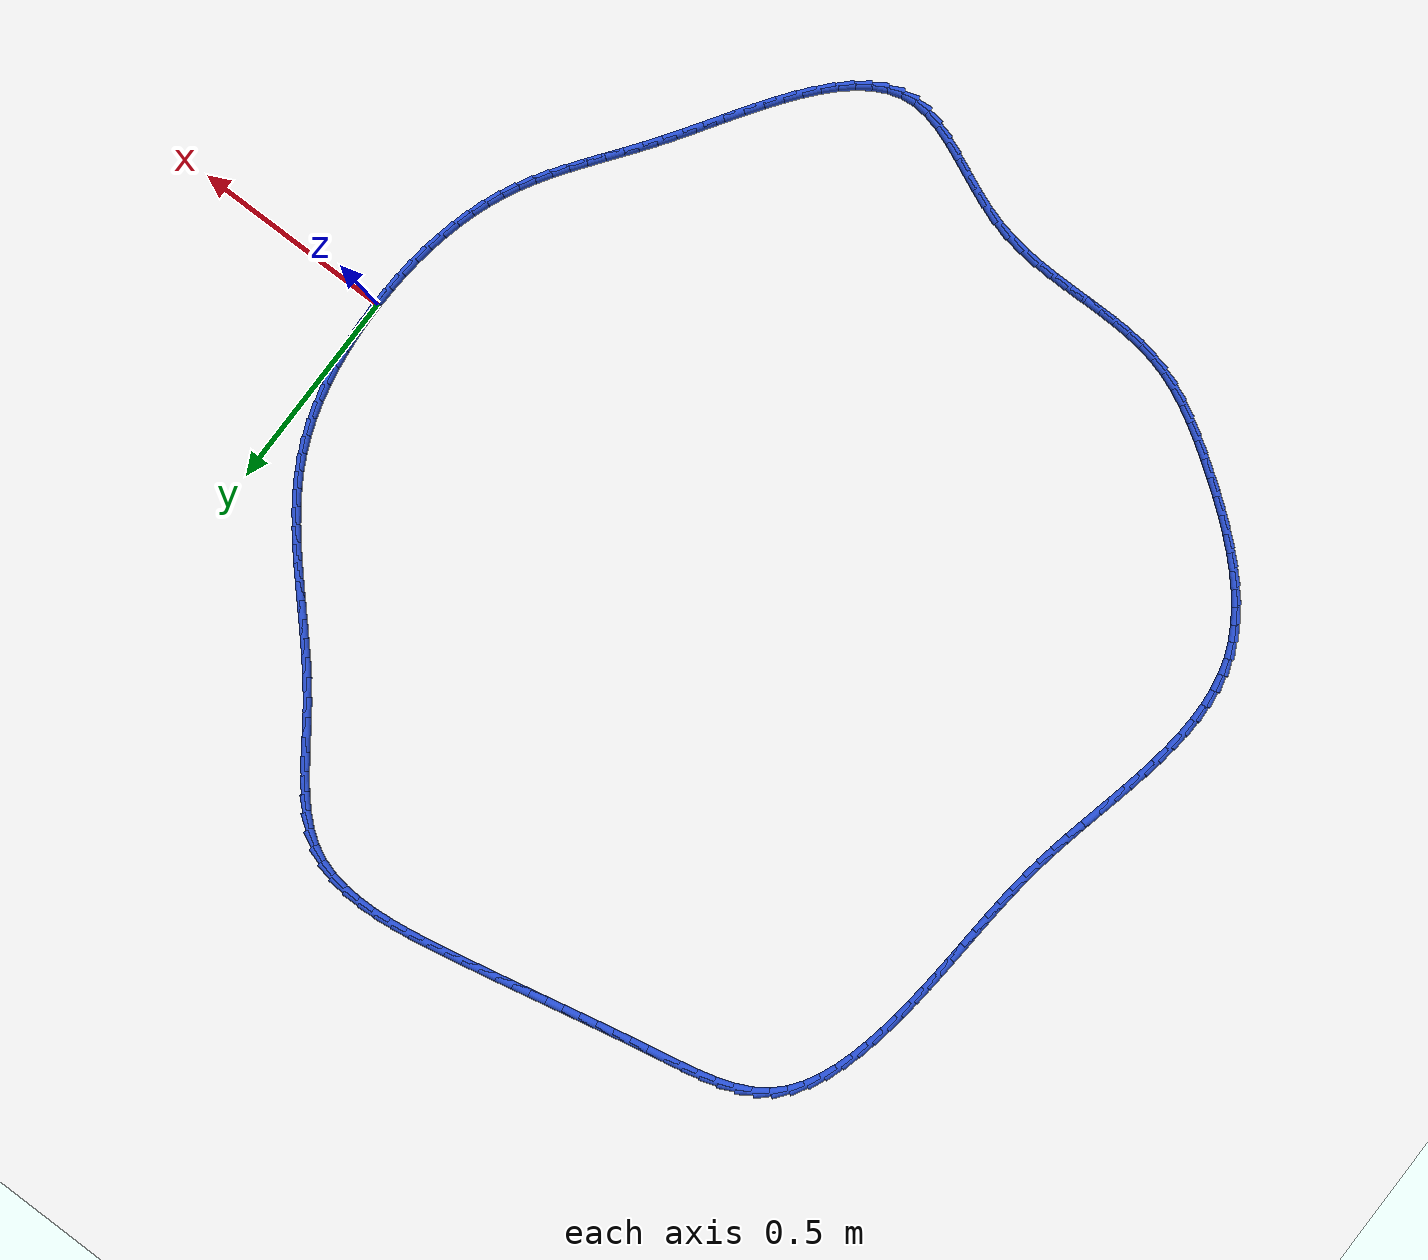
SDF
<sdf version="1.6">
 <world name="default">
  <light name="sun" type="directional">
   <pose>0 0 10 0 -0 0</pose>
   <diffuse>0.8 0.8 0.8 1</diffuse>
   <specular>0.2 0.2 0.2 1</specular>
   <attenuation>
    <range>1000</range>
    <constant>0.9</constant>
    <linear>0.01</linear>
    <quadratic>0.001</quadratic>
   </attenuation>
   <direction>-0.5 0.1 -0.9</direction>
  </light>
  <model name="ground_plane">
   <static>1</static>
   <link name="link">
    <collision name="collision">
     <geometry><plane><normal>0 0 1</normal><size>100 100</size></plane></geometry>
     <surface><friction><ode><mu>100</mu><mu2>50</mu2></ode></friction></surface>
    </collision>
    <visual name="visual">
     <cast_shadows>0</cast_shadows>
     <geometry><plane><normal>0 0 1</normal><size>100 100</size></plane></geometry>
     <material>
      <script><uri>file://media/materials/scripts/gazebo.material</uri><name>Gazebo/WhiteGlow</name></script>
     </material>
    </visual>
   </link>
  </model>
  <gravity>0 0 -9.8</gravity>
  <magnetic_field>6e-06 2.3e-05 -4.2e-05</magnetic_field>
  <atmosphere type="adiabatic"/>
  <physics name="default_physics" default="0" type="ode">
   <max_step_size>0.001</max_step_size>
   <real_time_factor>1</real_time_factor>
   <real_time_update_rate>1000</real_time_update_rate>
  </physics>
  <scene><ambient>0.4 0.4 0.4 1</ambient><background>0.7 0.7 0.7 1</background><shadows>1</shadows></scene>
  <spherical_coordinates>
   <surface_model>EARTH_WGS84</surface_model>
   <latitude_deg>0</latitude_deg>
   <longitude_deg>0</longitude_deg>
   <elevation>0</elevation>
   <heading_deg>0</heading_deg>
  </spherical_coordinates>
  <model name="line">
   <link name="link_0">
    <pose>4.336808689942018e-18 -1.3877787807814457e-17 0.01 0 1.57 -1.5573718621784105</pose>
    <collision name="collision">
     <geometry><cylinder><radius>0.01</radius><length>0.08</length></cylinder></geometry>
    </collision>
    <visual name="visual">
     <material>
      <script><name>Gazebo/Blue</name><uri>file://media/materials/scripts/gazebo.material</uri></script>
     </material>
     <geometry><cylinder><radius>0.01</radius><length>0.08</length></cylinder></geometry>
    </visual>
   </link>
   <link name="link_1">
    <pose>-0.0005983916359873998 0.04457203367264502 0.01 0 1.57 -1.5188670011490113</pose>
    <collision name="collision">
     <geometry><cylinder><radius>0.01</radius><length>0.08</length></cylinder></geometry>
    </collision>
    <visual name="visual">
     <material>
      <script><name>Gazebo/Blue</name><uri>file://media/materials/scripts/gazebo.material</uri></script>
     </material>
     <geometry><cylinder><radius>0.01</radius><length>0.08</length></cylinder></geometry>
    </visual>
   </link>
   <link name="link_2">
    <pose>-0.0029063172632489377 0.08897566622336017 0.01 0 1.57 -1.4777067448218728</pose>
    <collision name="collision">
     <geometry><cylinder><radius>0.01</radius><length>0.08</length></cylinder></geometry>
    </collision>
    <visual name="visual">
     <material>
      <script><name>Gazebo/Blue</name><uri>file://media/materials/scripts/gazebo.material</uri></script>
     </material>
     <geometry><cylinder><radius>0.01</radius><length>0.08</length></cylinder></geometry>
    </visual>
   </link>
   <link name="link_3">
    <pose>-0.007019723194135353 0.13303556172974781 0.01 0 1.57 -1.4335227655718614</pose>
    <collision name="collision">
     <geometry><cylinder><radius>0.01</radius><length>0.08</length></cylinder></geometry>
    </collision>
    <visual name="visual">
     <material>
      <script><name>Gazebo/Blue</name><uri>file://media/materials/scripts/gazebo.material</uri></script>
     </material>
     <geometry><cylinder><radius>0.01</radius><length>0.08</length></cylinder></geometry>
    </visual>
   </link>
   <link name="link_4">
    <pose>-0.013034555740997373 0.17657638426941008 0.01 0 1.57 -1.385933105360552</pose>
    <collision name="collision">
     <geometry><cylinder><radius>0.01</radius><length>0.08</length></cylinder></geometry>
    </collision>
    <visual name="visual">
     <material>
      <script><name>Gazebo/Blue</name><uri>file://media/materials/scripts/gazebo.material</uri></script>
     </material>
     <geometry><cylinder><radius>0.01</radius><length>0.08</length></cylinder></geometry>
    </visual>
   </link>
   <link name="link_5">
    <pose>-0.021046761216185737 0.21942279791994926 0.01 0 1.57 -1.3345503823095883</pose>
    <collision name="collision">
     <geometry><cylinder><radius>0.01</radius><length>0.08</length></cylinder></geometry>
    </collision>
    <visual name="visual">
     <material>
      <script><name>Gazebo/Blue</name><uri>file://media/materials/scripts/gazebo.material</uri></script>
     </material>
     <geometry><cylinder><radius>0.01</radius><length>0.08</length></cylinder></geometry>
    </visual>
   </link>
   <link name="link_6">
    <pose>-0.0311522859320512 0.26139946675896764 0.01 0 1.57 -1.2789963268459807</pose>
    <collision name="collision">
     <geometry><cylinder><radius>0.01</radius><length>0.08</length></cylinder></geometry>
    </collision>
    <visual name="visual">
     <material>
      <script><name>Gazebo/Blue</name><uri>file://media/materials/scripts/gazebo.material</uri></script>
     </material>
     <geometry><cylinder><radius>0.01</radius><length>0.08</length></cylinder></geometry>
    </visual>
   </link>
   <link name="link_7">
    <pose>-0.04344707620094446 0.3023310548640673 0.01 0 1.57 -1.2189245359871548</pose>
    <collision name="collision">
     <geometry><cylinder><radius>0.01</radius><length>0.08</length></cylinder></geometry>
    </collision>
    <visual name="visual">
     <material>
      <script><name>Gazebo/Blue</name><uri>file://media/materials/scripts/gazebo.material</uri></script>
     </material>
     <geometry><cylinder><radius>0.01</radius><length>0.08</length></cylinder></geometry>
    </visual>
   </link>
   <link name="link_8">
    <pose>-0.058027078335216295 0.34204222631285075 0.01 0 1.57 -1.1540531137541636</pose>
    <collision name="collision">
     <geometry><cylinder><radius>0.01</radius><length>0.08</length></cylinder></geometry>
    </collision>
    <visual name="visual">
     <material>
      <script><name>Gazebo/Blue</name><uri>file://media/materials/scripts/gazebo.material</uri></script>
     </material>
     <geometry><cylinder><radius>0.01</radius><length>0.08</length></cylinder></geometry>
    </visual>
   </link>
   <link name="link_9">
    <pose>-0.07498823864721739 0.38035764518291987 0.01 0 1.57 -1.0858827836086442</pose>
    <collision name="collision">
     <geometry><cylinder><radius>0.01</radius><length>0.08</length></cylinder></geometry>
    </collision>
    <visual name="visual">
     <material>
      <script><name>Gazebo/Blue</name><uri>file://media/materials/scripts/gazebo.material</uri></script>
     </material>
     <geometry><cylinder><radius>0.01</radius><length>0.08</length></cylinder></geometry>
    </visual>
   </link>
   <link name="link_10">
    <pose>-0.0943766519901181 0.4171567272831883 0.01 0 1.57 -1.0228177106142808</pose>
    <collision name="collision">
     <geometry><cylinder><radius>0.01</radius><length>0.08</length></cylinder></geometry>
    </collision>
    <visual name="visual">
     <material>
      <script><name>Gazebo/Blue</name><uri>file://media/materials/scripts/gazebo.material</uri></script>
     </material>
     <geometry><cylinder><radius>0.01</radius><length>0.08</length></cylinder></geometry>
    </visual>
   </link>
   <link name="link_11">
    <pose>-0.11599814226122311 0.4525827774046317 0.01 0 1.57 -0.9680428558615343</pose>
    <collision name="collision">
     <geometry><cylinder><radius>0.01</radius><length>0.08</length></cylinder></geometry>
    </collision>
    <visual name="visual">
     <material>
      <script><name>Gazebo/Blue</name><uri>file://media/materials/scripts/gazebo.material</uri></script>
     </material>
     <geometry><cylinder><radius>0.01</radius><length>0.08</length></cylinder></geometry>
    </visual>
   </link>
   <link name="link_12">
    <pose>-0.1395862384832859 0.4868585016157743 0.01 0 1.57 -0.921997925332311</pose>
    <collision name="collision">
     <geometry><cylinder><radius>0.01</radius><length>0.08</length></cylinder></geometry>
    </collision>
    <visual name="visual">
     <material>
      <script><name>Gazebo/Blue</name><uri>file://media/materials/scripts/gazebo.material</uri></script>
     </material>
     <geometry><cylinder><radius>0.01</radius><length>0.08</length></cylinder></geometry>
    </visual>
   </link>
   <link name="link_13">
    <pose>-0.1648744552800054 0.5202066217995853 0.01 0 1.57 -0.8848145867729409</pose>
    <collision name="collision">
     <geometry><cylinder><radius>0.01</radius><length>0.08</length></cylinder></geometry>
    </collision>
    <visual name="visual">
     <material>
      <script><name>Gazebo/Blue</name><uri>file://media/materials/scripts/gazebo.material</uri></script>
     </material>
     <geometry><cylinder><radius>0.01</radius><length>0.08</length></cylinder></geometry>
    </visual>
   </link>
   <link name="link_14">
    <pose>-0.1915963072750807 0.5528498598390348 0.01 0 1.57 -0.85642039293689</pose>
    <collision name="collision">
     <geometry><cylinder><radius>0.01</radius><length>0.08</length></cylinder></geometry>
    </collision>
    <visual name="visual">
     <material>
      <script><name>Gazebo/Blue</name><uri>file://media/materials/scripts/gazebo.material</uri></script>
     </material>
     <geometry><cylinder><radius>0.01</radius><length>0.08</length></cylinder></geometry>
    </visual>
   </link>
   <link name="link_15">
    <pose>-0.21948530909221053 0.5850109376170919 0.01 0 1.57 -0.8366287324983233</pose>
    <collision name="collision">
     <geometry><cylinder><radius>0.01</radius><length>0.08</length></cylinder></geometry>
    </collision>
    <visual name="visual">
     <material>
      <script><name>Gazebo/Blue</name><uri>file://media/materials/scripts/gazebo.material</uri></script>
     </material>
     <geometry><cylinder><radius>0.01</radius><length>0.08</length></cylinder></geometry>
    </visual>
   </link>
   <link name="link_16">
    <pose>-0.24827497535509394 0.6169125770167263 0.01 0 1.57 -0.8252062401643862</pose>
    <collision name="collision">
     <geometry><cylinder><radius>0.01</radius><length>0.08</length></cylinder></geometry>
    </collision>
    <visual name="visual">
     <material>
      <script><name>Gazebo/Blue</name><uri>file://media/materials/scripts/gazebo.material</uri></script>
     </material>
     <geometry><cylinder><radius>0.01</radius><length>0.08</length></cylinder></geometry>
    </visual>
   </link>
   <link name="link_17">
    <pose>-0.27769882068742996 0.6487774999209076 0.01 0 1.57 -0.8219165124980077</pose>
    <collision name="collision">
     <geometry><cylinder><radius>0.01</radius><length>0.08</length></cylinder></geometry>
    </collision>
    <visual name="visual">
     <material>
      <script><name>Gazebo/Blue</name><uri>file://media/materials/scripts/gazebo.material</uri></script>
     </material>
     <geometry><cylinder><radius>0.01</radius><length>0.08</length></cylinder></geometry>
    </visual>
   </link>
   <link name="link_18">
    <pose>-0.30749035971291716 0.6808284282126049 0.01 0 1.57 -0.8265426815719641</pose>
    <collision name="collision">
     <geometry><cylinder><radius>0.01</radius><length>0.08</length></cylinder></geometry>
    </collision>
    <visual name="visual">
     <material>
      <script><name>Gazebo/Blue</name><uri>file://media/materials/scripts/gazebo.material</uri></script>
     </material>
     <geometry><cylinder><radius>0.01</radius><length>0.08</length></cylinder></geometry>
    </visual>
   </link>
   <link name="link_19">
    <pose>-0.33738310705525487 0.7132880837747883 0.01 0 1.57 -0.8388922984775231</pose>
    <collision name="collision">
     <geometry><cylinder><radius>0.01</radius><length>0.08</length></cylinder></geometry>
    </collision>
    <visual name="visual">
     <material>
      <script><name>Gazebo/Blue</name><uri>file://media/materials/scripts/gazebo.material</uri></script>
     </material>
     <geometry><cylinder><radius>0.01</radius><length>0.08</length></cylinder></geometry>
    </visual>
   </link>
   <link name="link_20">
    <pose>-0.36711057733814195 0.7463791884904272 0.01 0 1.57 -0.8587875560523728</pose>
    <collision name="collision">
     <geometry><cylinder><radius>0.01</radius><length>0.08</length></cylinder></geometry>
    </collision>
    <visual name="visual">
     <material>
      <script><name>Gazebo/Blue</name><uri>file://media/materials/scripts/gazebo.material</uri></script>
     </material>
     <geometry><cylinder><radius>0.01</radius><length>0.08</length></cylinder></geometry>
    </visual>
   </link>
   <link name="link_21">
    <pose>-0.39640628518527715 0.7803244642424909 0.01 0 1.57 -0.8860432194951134</pose>
    <collision name="collision">
     <geometry><cylinder><radius>0.01</radius><length>0.08</length></cylinder></geometry>
    </collision>
    <visual name="visual">
     <material>
      <script><name>Gazebo/Blue</name><uri>file://media/materials/scripts/gazebo.material</uri></script>
     </material>
     <geometry><cylinder><radius>0.01</radius><length>0.08</length></cylinder></geometry>
    </visual>
   </link>
   <link name="link_22">
    <pose>-0.4250037452203595 0.8153466329139489 0.01 0 1.57 -0.9198748710210024</pose>
    <collision name="collision">
     <geometry><cylinder><radius>0.01</radius><length>0.08</length></cylinder></geometry>
    </collision>
    <visual name="visual">
     <material>
      <script><name>Gazebo/Blue</name><uri>file://media/materials/scripts/gazebo.material</uri></script>
     </material>
     <geometry><cylinder><radius>0.01</radius><length>0.08</length></cylinder></geometry>
    </visual>
   </link>
   <link name="link_23">
    <pose>-0.4526516445011673 0.8516461908384293 0.01 0 1.57 -0.9465608460449983</pose>
    <collision name="collision">
     <geometry><cylinder><radius>0.01</radius><length>0.08</length></cylinder></geometry>
    </collision>
    <visual name="visual">
     <material>
      <script><name>Gazebo/Blue</name><uri>file://media/materials/scripts/gazebo.material</uri></script>
     </material>
     <geometry><cylinder><radius>0.01</radius><length>0.08</length></cylinder></geometry>
    </visual>
   </link>
   <link name="link_24">
    <pose>-0.4794708626833767 0.8888784228886962 0.01 0 1.57 -0.9525758931506126</pose>
    <collision name="collision">
     <geometry><cylinder><radius>0.01</radius><length>0.08</length></cylinder></geometry>
    </collision>
    <visual name="visual">
     <material>
      <script><name>Gazebo/Blue</name><uri>file://media/materials/scripts/gazebo.material</uri></script>
     </material>
     <geometry><cylinder><radius>0.01</radius><length>0.08</length></cylinder></geometry>
    </visual>
   </link>
   <link name="link_25">
    <pose>-0.5059678521182613 0.9261338024559791 0.01 0 1.57 -0.9371956523138425</pose>
    <collision name="collision">
     <geometry><cylinder><radius>0.01</radius><length>0.08</length></cylinder></geometry>
    </collision>
    <visual name="visual">
     <material>
      <script><name>Gazebo/Blue</name><uri>file://media/materials/scripts/gazebo.material</uri></script>
     </material>
     <geometry><cylinder><radius>0.01</radius><length>0.08</length></cylinder></geometry>
    </visual>
   </link>
   <link name="link_26">
    <pose>-0.5326669146571629 0.9624766558451245 0.01 0 1.57 -0.8990727459790173</pose>
    <collision name="collision">
     <geometry><cylinder><radius>0.01</radius><length>0.08</length></cylinder></geometry>
    </collision>
    <visual name="visual">
     <material>
      <script><name>Gazebo/Blue</name><uri>file://media/materials/scripts/gazebo.material</uri></script>
     </material>
     <geometry><cylinder><radius>0.01</radius><length>0.08</length></cylinder></geometry>
    </visual>
   </link>
   <link name="link_27">
    <pose>-0.5600923521514234 0.9969713093609789 0.01 0 1.57 -0.8356096361105354</pose>
    <collision name="collision">
     <geometry><cylinder><radius>0.01</radius><length>0.08</length></cylinder></geometry>
    </collision>
    <visual name="visual">
     <material>
      <script><name>Gazebo/Blue</name><uri>file://media/materials/scripts/gazebo.material</uri></script>
     </material>
     <geometry><cylinder><radius>0.01</radius><length>0.08</length></cylinder></geometry>
    </visual>
   </link>
   <link name="link_28">
    <pose>-0.5887684664523848 1.0286820893083894 0.01 0 1.57 -0.7433326028633387</pose>
    <collision name="collision">
     <geometry><cylinder><radius>0.01</radius><length>0.08</length></cylinder></geometry>
    </collision>
    <visual name="visual">
     <material>
      <script><name>Gazebo/Blue</name><uri>file://media/materials/scripts/gazebo.material</uri></script>
     </material>
     <geometry><cylinder><radius>0.01</radius><length>0.08</length></cylinder></geometry>
    </visual>
   </link>
   <link name="link_29">
    <pose>-0.6192195594113888 1.0566733219922024 0.01 0 1.57 -0.6190938128711576</pose>
    <collision name="collision">
     <geometry><cylinder><radius>0.01</radius><length>0.08</length></cylinder></geometry>
    </collision>
    <visual name="visual">
     <material>
      <script><name>Gazebo/Blue</name><uri>file://media/materials/scripts/gazebo.material</uri></script>
     </material>
     <geometry><cylinder><radius>0.01</radius><length>0.08</length></cylinder></geometry>
    </visual>
   </link>
   <link name="link_30">
    <pose>-0.6519699328797776 1.0800093337172654 0.01 0 1.57 -0.46355464956341375</pose>
    <collision name="collision">
     <geometry><cylinder><radius>0.01</radius><length>0.08</length></cylinder></geometry>
    </collision>
    <visual name="visual">
     <material>
      <script><name>Gazebo/Blue</name><uri>file://media/materials/scripts/gazebo.material</uri></script>
     </material>
     <geometry><cylinder><radius>0.01</radius><length>0.08</length></cylinder></geometry>
    </visual>
   </link>
   <link name="link_31">
    <pose>-0.6875261806087714 1.0977833261627967 0.01 0 1.57 -0.30430831552342846</pose>
    <collision name="collision">
     <geometry><cylinder><radius>0.01</radius><length>0.08</length></cylinder></geometry>
    </collision>
    <visual name="visual">
     <material>
      <script><name>Gazebo/Blue</name><uri>file://media/materials/scripts/gazebo.material</uri></script>
     </material>
     <geometry><cylinder><radius>0.01</radius><length>0.08</length></cylinder></geometry>
    </visual>
   </link>
   <link name="link_32">
    <pose>-0.7259310410927117 1.1098448777003238 0.01 0 1.57 -0.170162189055109</pose>
    <collision name="collision">
     <geometry><cylinder><radius>0.01</radius><length>0.08</length></cylinder></geometry>
    </collision>
    <visual name="visual">
     <material>
      <script><name>Gazebo/Blue</name><uri>file://media/materials/scripts/gazebo.material</uri></script>
     </material>
     <geometry><cylinder><radius>0.01</radius><length>0.08</length></cylinder></geometry>
    </visual>
   </link>
   <link name="link_33">
    <pose>-0.7667296076741336 1.116855042238805 0.01 0 1.57 -0.06218998261864441</pose>
    <collision name="collision">
     <geometry><cylinder><radius>0.01</radius><length>0.08</length></cylinder></geometry>
    </collision>
    <visual name="visual">
     <material>
      <script><name>Gazebo/Blue</name><uri>file://media/materials/scripts/gazebo.material</uri></script>
     </material>
     <geometry><cylinder><radius>0.01</radius><length>0.08</length></cylinder></geometry>
    </visual>
   </link>
   <link name="link_34">
    <pose>-0.8094424971405626 1.119514785912926 0.01 0 1.57 0.022414359313585354</pose>
    <collision name="collision">
     <geometry><cylinder><radius>0.01</radius><length>0.08</length></cylinder></geometry>
    </collision>
    <visual name="visual">
     <material>
      <script><name>Gazebo/Blue</name><uri>file://media/materials/scripts/gazebo.material</uri></script>
     </material>
     <geometry><cylinder><radius>0.01</radius><length>0.08</length></cylinder></geometry>
    </visual>
   </link>
   <link name="link_35">
    <pose>-0.8535903262795242 1.1185250748573716 0.01 0 1.57 0.08709406145094067</pose>
    <collision name="collision">
     <geometry><cylinder><radius>0.01</radius><length>0.08</length></cylinder></geometry>
    </collision>
    <visual name="visual">
     <material>
      <script><name>Gazebo/Blue</name><uri>file://media/materials/scripts/gazebo.material</uri></script>
     </material>
     <geometry><cylinder><radius>0.01</radius><length>0.08</length></cylinder></geometry>
    </visual>
   </link>
   <link name="link_36">
    <pose>-0.8986937118785445 1.1145868752068282 0.01 0 1.57 0.13488854308228868</pose>
    <collision name="collision">
     <geometry><cylinder><radius>0.01</radius><length>0.08</length></cylinder></geometry>
    </collision>
    <visual name="visual">
     <material>
      <script><name>Gazebo/Blue</name><uri>file://media/materials/scripts/gazebo.material</uri></script>
     </material>
     <geometry><cylinder><radius>0.01</radius><length>0.08</length></cylinder></geometry>
    </visual>
   </link>
   <link name="link_37">
    <pose>-0.944273270725149 1.108401153095981 0.01 0 1.57 0.16805531831534667</pose>
    <collision name="collision">
     <geometry><cylinder><radius>0.01</radius><length>0.08</length></cylinder></geometry>
    </collision>
    <visual name="visual">
     <material>
      <script><name>Gazebo/Blue</name><uri>file://media/materials/scripts/gazebo.material</uri></script>
     </material>
     <geometry><cylinder><radius>0.01</radius><length>0.08</length></cylinder></geometry>
    </visual>
   </link>
   <link name="link_38">
    <pose>-0.9898496196068629 1.100668874659515 0.01 0 1.57 0.18797714940929328</pose>
    <collision name="collision">
     <geometry><cylinder><radius>0.01</radius><length>0.08</length></cylinder></geometry>
    </collision>
    <visual name="visual">
     <material>
      <script><name>Gazebo/Blue</name><uri>file://media/materials/scripts/gazebo.material</uri></script>
     </material>
     <geometry><cylinder><radius>0.01</radius><length>0.08</length></cylinder></geometry>
    </visual>
   </link>
   <link name="link_39">
    <pose>-1.034943375311212 1.092091006032116 0.01 0 1.57 0.19647220726962114</pose>
    <collision name="collision">
     <geometry><cylinder><radius>0.01</radius><length>0.08</length></cylinder></geometry>
    </collision>
    <visual name="visual">
     <material>
      <script><name>Gazebo/Blue</name><uri>file://media/materials/scripts/gazebo.material</uri></script>
     </material>
     <geometry><cylinder><radius>0.01</radius><length>0.08</length></cylinder></geometry>
    </visual>
   </link>
   <link name="link_40">
    <pose>-1.0791437507667074 1.0832933681481307 0.01 0 1.57 0.2013810168366769</pose>
    <collision name="collision">
     <geometry><cylinder><radius>0.01</radius><length>0.08</length></cylinder></geometry>
    </collision>
    <visual name="visual">
     <material>
      <script><name>Gazebo/Blue</name><uri>file://media/materials/scripts/gazebo.material</uri></script>
     </material>
     <geometry><cylinder><radius>0.01</radius><length>0.08</length></cylinder></geometry>
    </visual>
   </link>
   <link name="link_41">
    <pose>-1.1224501323341165 1.0744524481412294 0.01 0 1.57 0.2055438187705518</pose>
    <collision name="collision">
     <geometry><cylinder><radius>0.01</radius><length>0.08</length></cylinder></geometry>
    </collision>
    <visual name="visual">
     <material>
      <script><name>Gazebo/Blue</name><uri>file://media/materials/scripts/gazebo.material</uri></script>
     </material>
     <geometry><cylinder><radius>0.01</radius><length>0.08</length></cylinder></geometry>
    </visual>
   </link>
   <link name="link_42">
    <pose>-1.1650137014224726 1.0655784458124642 0.01 0 1.57 0.2088853066940639</pose>
    <collision name="collision">
     <geometry><cylinder><radius>0.01</radius><length>0.08</length></cylinder></geometry>
    </collision>
    <visual name="visual">
     <material>
      <script><name>Gazebo/Blue</name><uri>file://media/materials/scripts/gazebo.material</uri></script>
     </material>
     <geometry><cylinder><radius>0.01</radius><length>0.08</length></cylinder></geometry>
    </visual>
   </link>
   <link name="link_43">
    <pose>-1.2069858849518516 1.0566812920122384 0.01 0 1.57 0.21133761397616224</pose>
    <collision name="collision">
     <geometry><cylinder><radius>0.01</radius><length>0.08</length></cylinder></geometry>
    </collision>
    <visual name="visual">
     <material>
      <script><name>Gazebo/Blue</name><uri>file://media/materials/scripts/gazebo.material</uri></script>
     </material>
     <geometry><cylinder><radius>0.01</radius><length>0.08</length></cylinder></geometry>
    </visual>
   </link>
   <link name="link_44">
    <pose>-1.2485181098423315 1.0477709175909564 0.01 0 1.57 0.21284821752443886</pose>
    <collision name="collision">
     <geometry><cylinder><radius>0.01</radius><length>0.08</length></cylinder></geometry>
    </collision>
    <visual name="visual">
     <material>
      <script><name>Gazebo/Blue</name><uri>file://media/materials/scripts/gazebo.material</uri></script>
     </material>
     <geometry><cylinder><radius>0.01</radius><length>0.08</length></cylinder></geometry>
    </visual>
   </link>
   <link name="link_45">
    <pose>-1.289761803013988 1.0388572533990221 0.01 0 1.57 0.21338248231466686</pose>
    <collision name="collision">
     <geometry><cylinder><radius>0.01</radius><length>0.08</length></cylinder></geometry>
    </collision>
    <visual name="visual">
     <material>
      <script><name>Gazebo/Blue</name><uri>file://media/materials/scripts/gazebo.material</uri></script>
     </material>
     <geometry><cylinder><radius>0.01</radius><length>0.08</length></cylinder></geometry>
    </visual>
   </link>
   <link name="link_46">
    <pose>-1.3308683913868986 1.0299502302868395 0.01 0 1.57 0.21292542087547967</pose>
    <collision name="collision">
     <geometry><cylinder><radius>0.01</radius><length>0.08</length></cylinder></geometry>
    </collision>
    <visual name="visual">
     <material>
      <script><name>Gazebo/Blue</name><uri>file://media/materials/scripts/gazebo.material</uri></script>
     </material>
     <geometry><cylinder><radius>0.01</radius><length>0.08</length></cylinder></geometry>
    </visual>
   </link>
   <link name="link_47">
    <pose>-1.3719893018811395 1.0210597791048124 0.01 0 1.57 0.21148251123334244</pose>
    <collision name="collision">
     <geometry><cylinder><radius>0.01</radius><length>0.08</length></cylinder></geometry>
    </collision>
    <visual name="visual">
     <material>
      <script><name>Gazebo/Blue</name><uri>file://media/materials/scripts/gazebo.material</uri></script>
     </material>
     <geometry><cylinder><radius>0.01</radius><length>0.08</length></cylinder></geometry>
    </visual>
   </link>
   <link name="link_48">
    <pose>-1.4132759614167878 1.0121958307033445 0.01 0 1.57 0.20907949669364362</pose>
    <collision name="collision">
     <geometry><cylinder><radius>0.01</radius><length>0.08</length></cylinder></geometry>
    </collision>
    <visual name="visual">
     <material>
      <script><name>Gazebo/Blue</name><uri>file://media/materials/scripts/gazebo.material</uri></script>
     </material>
     <geometry><cylinder><radius>0.01</radius><length>0.08</length></cylinder></geometry>
    </visual>
   </link>
   <link name="link_49">
    <pose>-1.45487979691392 1.0033683159328401 0.01 0 1.57 0.20576118155316644</pose>
    <collision name="collision">
     <geometry><cylinder><radius>0.01</radius><length>0.08</length></cylinder></geometry>
    </collision>
    <visual name="visual">
     <material>
      <script><name>Gazebo/Blue</name><uri>file://media/materials/scripts/gazebo.material</uri></script>
     </material>
     <geometry><cylinder><radius>0.01</radius><length>0.08</length></cylinder></geometry>
    </visual>
   </link>
   <link name="link_50">
    <pose>-1.4969522352926135 0.9945871656437031 0.01 0 1.57 0.2015893260123306</pose>
    <collision name="collision">
     <geometry><cylinder><radius>0.01</radius><length>0.08</length></cylinder></geometry>
    </collision>
    <visual name="visual">
     <material>
      <script><name>Gazebo/Blue</name><uri>file://media/materials/scripts/gazebo.material</uri></script>
     </material>
     <geometry><cylinder><radius>0.01</radius><length>0.08</length></cylinder></geometry>
    </visual>
   </link>
   <link name="link_51">
    <pose>-1.5396447034729444 0.9858623106863369 0.01 0 1.57 0.1966398228140414</pose>
    <collision name="collision">
     <geometry><cylinder><radius>0.01</radius><length>0.08</length></cylinder></geometry>
    </collision>
    <visual name="visual">
     <material>
      <script><name>Gazebo/Blue</name><uri>file://media/materials/scripts/gazebo.material</uri></script>
     </material>
     <geometry><cylinder><radius>0.01</radius><length>0.08</length></cylinder></geometry>
    </visual>
   </link>
   <link name="link_52">
    <pose>-1.5831086282129405 0.9772036817717993 0.01 0 1.57 0.19546544410255354</pose>
    <collision name="collision">
     <geometry><cylinder><radius>0.01</radius><length>0.08</length></cylinder></geometry>
    </collision>
    <visual name="visual">
     <material>
      <script><name>Gazebo/Blue</name><uri>file://media/materials/scripts/gazebo.material</uri></script>
     </material>
     <geometry><cylinder><radius>0.01</radius><length>0.08</length></cylinder></geometry>
    </visual>
   </link>
   <link name="link_53">
    <pose>-1.6273008761709957 0.968453906059973 0.01 0 1.57 0.2152977972804454</pose>
    <collision name="collision">
     <geometry><cylinder><radius>0.01</radius><length>0.08</length></cylinder></geometry>
    </collision>
    <visual name="visual">
     <material>
      <script><name>Gazebo/Blue</name><uri>file://media/materials/scripts/gazebo.material</uri></script>
     </material>
     <geometry><cylinder><radius>0.01</radius><length>0.08</length></cylinder></geometry>
    </visual>
   </link>
   <link name="link_54">
    <pose>-1.6714219336706635 0.9588051941233023 0.01 0 1.57 0.26123214382009385</pose>
    <collision name="collision">
     <geometry><cylinder><radius>0.01</radius><length>0.08</length></cylinder></geometry>
    </collision>
    <visual name="visual">
     <material>
      <script><name>Gazebo/Blue</name><uri>file://media/materials/scripts/gazebo.material</uri></script>
     </material>
     <geometry><cylinder><radius>0.01</radius><length>0.08</length></cylinder></geometry>
    </visual>
   </link>
   <link name="link_55">
    <pose>-1.7144885043078126 0.9472917205183986 0.01 0 1.57 0.3363270422374548</pose>
    <collision name="collision">
     <geometry><cylinder><radius>0.01</radius><length>0.08</length></cylinder></geometry>
    </collision>
    <visual name="visual">
     <material>
      <script><name>Gazebo/Blue</name><uri>file://media/materials/scripts/gazebo.material</uri></script>
     </material>
     <geometry><cylinder><radius>0.01</radius><length>0.08</length></cylinder></geometry>
    </visual>
   </link>
   <link name="link_56">
    <pose>-1.7555172916783093 0.932947659801871 0.01 0 1.57 0.4453102789506229</pose>
    <collision name="collision">
     <geometry><cylinder><radius>0.01</radius><length>0.08</length></cylinder></geometry>
    </collision>
    <visual name="visual">
     <material>
      <script><name>Gazebo/Blue</name><uri>file://media/materials/scripts/gazebo.material</uri></script>
     </material>
     <geometry><cylinder><radius>0.01</radius><length>0.08</length></cylinder></geometry>
    </visual>
   </link>
   <link name="link_57">
    <pose>-1.79352499937802 0.9148071865303304 0.01 0 1.57 0.5927481524676262</pose>
    <collision name="collision">
     <geometry><cylinder><radius>0.01</radius><length>0.08</length></cylinder></geometry>
    </collision>
    <visual name="visual">
     <material>
      <script><name>Gazebo/Blue</name><uri>file://media/materials/scripts/gazebo.material</uri></script>
     </material>
     <geometry><cylinder><radius>0.01</radius><length>0.08</length></cylinder></geometry>
    </visual>
   </link>
   <link name="link_58">
    <pose>-1.8275283310028125 0.8919044752603865 0.01 0 1.57 0.7719658007799016</pose>
    <collision name="collision">
     <geometry><cylinder><radius>0.01</radius><length>0.08</length></cylinder></geometry>
    </collision>
    <visual name="visual">
     <material>
      <script><name>Gazebo/Blue</name><uri>file://media/materials/scripts/gazebo.material</uri></script>
     </material>
     <geometry><cylinder><radius>0.01</radius><length>0.08</length></cylinder></geometry>
    </visual>
   </link>
   <link name="link_59">
    <pose>-1.8567161494937785 0.8634904323961726 0.01 0 1.57 0.9380922472657424</pose>
    <collision name="collision">
     <geometry><cylinder><radius>0.01</radius><length>0.08</length></cylinder></geometry>
    </collision>
    <visual name="visual">
     <material>
      <script><name>Gazebo/Blue</name><uri>file://media/materials/scripts/gazebo.material</uri></script>
     </material>
     <geometry><cylinder><radius>0.01</radius><length>0.08</length></cylinder></geometry>
    </visual>
   </link>
   <link name="link_60">
    <pose>-1.8812467838868188 0.8300364277303285 0.01 0 1.57 1.0742404394073841</pose>
    <collision name="collision">
     <geometry><cylinder><radius>0.01</radius><length>0.08</length></cylinder></geometry>
    </collision>
    <visual name="visual">
     <material>
      <script><name>Gazebo/Blue</name><uri>file://media/materials/scripts/gazebo.material</uri></script>
     </material>
     <geometry><cylinder><radius>0.01</radius><length>0.08</length></cylinder></geometry>
    </visual>
   </link>
   <link name="link_61">
    <pose>-1.901617623968946 0.7924406755170287 0.01 0 1.57 1.1824357154309286</pose>
    <collision name="collision">
     <geometry><cylinder><radius>0.01</radius><length>0.08</length></cylinder></geometry>
    </collision>
    <visual name="visual">
     <material>
      <script><name>Gazebo/Blue</name><uri>file://media/materials/scripts/gazebo.material</uri></script>
     </material>
     <geometry><cylinder><radius>0.01</radius><length>0.08</length></cylinder></geometry>
    </visual>
   </link>
   <link name="link_62">
    <pose>-1.9183264173494723 0.7516018404738722 0.01 0 1.57 1.2668627036573386</pose>
    <collision name="collision">
     <geometry><cylinder><radius>0.01</radius><length>0.08</length></cylinder></geometry>
    </collision>
    <visual name="visual">
     <material>
      <script><name>Gazebo/Blue</name><uri>file://media/materials/scripts/gazebo.material</uri></script>
     </material>
     <geometry><cylinder><radius>0.01</radius><length>0.08</length></cylinder></geometry>
    </visual>
   </link>
   <link name="link_63">
    <pose>-1.9318709116377106 0.7084185873184566 0.01 0 1.57 1.3317165968595035</pose>
    <collision name="collision">
     <geometry><cylinder><radius>0.01</radius><length>0.08</length></cylinder></geometry>
    </collision>
    <visual name="visual">
     <material>
      <script><name>Gazebo/Blue</name><uri>file://media/materials/scripts/gazebo.material</uri></script>
     </material>
     <geometry><cylinder><radius>0.01</radius><length>0.08</length></cylinder></geometry>
    </visual>
   </link>
   <link name="link_64">
    <pose>-1.9427488544429725 0.6637895807683813 0.01 0 1.57 1.3803506667457155</pose>
    <collision name="collision">
     <geometry><cylinder><radius>0.01</radius><length>0.08</length></cylinder></geometry>
    </collision>
    <visual name="visual">
     <material>
      <script><name>Gazebo/Blue</name><uri>file://media/materials/scripts/gazebo.material</uri></script>
     </material>
     <geometry><cylinder><radius>0.01</radius><length>0.08</length></cylinder></geometry>
    </visual>
   </link>
   <link name="link_65">
    <pose>-1.9514579933745724 0.6186134855412443 0.01 0 1.57 1.4152566017948995</pose>
    <collision name="collision">
     <geometry><cylinder><radius>0.01</radius><length>0.08</length></cylinder></geometry>
    </collision>
    <visual name="visual">
     <material>
      <script><name>Gazebo/Blue</name><uri>file://media/materials/scripts/gazebo.material</uri></script>
     </material>
     <geometry><cylinder><radius>0.01</radius><length>0.08</length></cylinder></geometry>
    </visual>
   </link>
   <link name="link_66">
    <pose>-1.9584903436504462 0.5737661109770493 0.01 0 1.57 1.4418287530583103</pose>
    <collision name="collision">
     <geometry><cylinder><radius>0.01</radius><length>0.08</length></cylinder></geometry>
    </collision>
    <visual name="visual">
     <material>
      <script><name>Gazebo/Blue</name><uri>file://media/materials/scripts/gazebo.material</uri></script>
     </material>
     <geometry><cylinder><radius>0.01</radius><length>0.08</length></cylinder></geometry>
    </visual>
   </link>
   <link name="link_67">
    <pose>-1.9642142279488908 0.5296300970708596 0.01 0 1.57 1.4640198442393648</pose>
    <collision name="collision">
     <geometry><cylinder><radius>0.01</radius><length>0.08</length></cylinder></geometry>
    </collision>
    <visual name="visual">
     <material>
      <script><name>Gazebo/Blue</name><uri>file://media/materials/scripts/gazebo.material</uri></script>
     </material>
     <geometry><cylinder><radius>0.01</radius><length>0.08</length></cylinder></geometry>
    </visual>
   </link>
   <link name="link_68">
    <pose>-1.9688786428658611 0.48611232379185343 0.01 0 1.57 1.4815455242399365</pose>
    <collision name="collision">
     <geometry><cylinder><radius>0.01</radius><length>0.08</length></cylinder></geometry>
    </collision>
    <visual name="visual">
     <material>
      <script><name>Gazebo/Blue</name><uri>file://media/materials/scripts/gazebo.material</uri></script>
     </material>
     <geometry><cylinder><radius>0.01</radius><length>0.08</length></cylinder></geometry>
    </visual>
   </link>
   <link name="link_69">
    <pose>-1.9727277262510086 0.44310029900528597 0.01 0 1.57 1.4940355642649603</pose>
    <collision name="collision">
     <geometry><cylinder><radius>0.01</radius><length>0.08</length></cylinder></geometry>
    </collision>
    <visual name="visual">
     <material>
      <script><name>Gazebo/Blue</name><uri>file://media/materials/scripts/gazebo.material</uri></script>
     </material>
     <geometry><cylinder><radius>0.01</radius><length>0.08</length></cylinder></geometry>
    </visual>
   </link>
   <link name="link_70">
    <pose>-1.9760056159539834 0.40048153057641045 0.01 0 1.57 1.501211807248619</pose>
    <collision name="collision">
     <geometry><cylinder><radius>0.01</radius><length>0.08</length></cylinder></geometry>
    </collision>
    <visual name="visual">
     <material>
      <script><name>Gazebo/Blue</name><uri>file://media/materials/scripts/gazebo.material</uri></script>
     </material>
     <geometry><cylinder><radius>0.01</radius><length>0.08</length></cylinder></geometry>
    </visual>
   </link>
   <link name="link_71">
    <pose>-1.9789564498244356 0.35814352637048047 0.01 0 1.57 1.5028920170929683</pose>
    <collision name="collision">
     <geometry><cylinder><radius>0.01</radius><length>0.08</length></cylinder></geometry>
    </collision>
    <visual name="visual">
     <material>
      <script><name>Gazebo/Blue</name><uri>file://media/materials/scripts/gazebo.material</uri></script>
     </material>
     <geometry><cylinder><radius>0.01</radius><length>0.08</length></cylinder></geometry>
    </visual>
   </link>
   <link name="link_72">
    <pose>-1.9818243657120163 0.31597379425275085 0.01 0 1.57 1.4989928508094597</pose>
    <collision name="collision">
     <geometry><cylinder><radius>0.01</radius><length>0.08</length></cylinder></geometry>
    </collision>
    <visual name="visual">
     <material>
      <script><name>Gazebo/Blue</name><uri>file://media/materials/scripts/gazebo.material</uri></script>
     </material>
     <geometry><cylinder><radius>0.01</radius><length>0.08</length></cylinder></geometry>
    </visual>
   </link>
   <link name="link_73">
    <pose>-1.9848535014663753 0.27385984208847464 0.01 0 1.57 1.4895329643839106</pose>
    <collision name="collision">
     <geometry><cylinder><radius>0.01</radius><length>0.08</length></cylinder></geometry>
    </collision>
    <visual name="visual">
     <material>
      <script><name>Gazebo/Blue</name><uri>file://media/materials/scripts/gazebo.material</uri></script>
     </material>
     <geometry><cylinder><radius>0.01</radius><length>0.08</length></cylinder></geometry>
    </visual>
   </link>
   <link name="link_74">
    <pose>-1.9882879949371643 0.23168917774290657 0.01 0 1.57 1.474636523252333</pose>
    <collision name="collision">
     <geometry><cylinder><radius>0.01</radius><length>0.08</length></cylinder></geometry>
    </collision>
    <visual name="visual">
     <material>
      <script><name>Gazebo/Blue</name><uri>file://media/materials/scripts/gazebo.material</uri></script>
     </material>
     <geometry><cylinder><radius>0.01</radius><length>0.08</length></cylinder></geometry>
    </visual>
   </link>
   <link name="link_75">
    <pose>-1.9923719839740315 0.1893493090813 0.01 0 1.57 1.454536499628216</pose>
    <collision name="collision">
     <geometry><cylinder><radius>0.01</radius><length>0.08</length></cylinder></geometry>
    </collision>
    <visual name="visual">
     <material>
      <script><name>Gazebo/Blue</name><uri>file://media/materials/scripts/gazebo.material</uri></script>
     </material>
     <geometry><cylinder><radius>0.01</radius><length>0.08</length></cylinder></geometry>
    </visual>
   </link>
   <link name="link_76">
    <pose>-1.9973496064266298 0.14672774396890864 0.01 0 1.57 1.4295762912710814</pose>
    <collision name="collision">
     <geometry><cylinder><radius>0.01</radius><length>0.08</length></cylinder></geometry>
    </collision>
    <visual name="visual">
     <material>
      <script><name>Gazebo/Blue</name><uri>file://media/materials/scripts/gazebo.material</uri></script>
     </material>
     <geometry><cylinder><radius>0.01</radius><length>0.08</length></cylinder></geometry>
    </visual>
   </link>
   <link name="link_77">
    <pose>-2.003465000144608 0.10371199027098711 0.01 0 1.57 1.4005641741584973</pose>
    <collision name="collision">
     <geometry><cylinder><radius>0.01</radius><length>0.08</length></cylinder></geometry>
    </collision>
    <visual name="visual">
     <material>
      <script><name>Gazebo/Blue</name><uri>file://media/materials/scripts/gazebo.material</uri></script>
     </material>
     <geometry><cylinder><radius>0.01</radius><length>0.08</length></cylinder></geometry>
    </visual>
   </link>
   <link name="link_78">
    <pose>-2.010945220504991 0.06019598072199666 0.01 0 1.57 1.3745747473614855</pose>
    <collision name="collision">
     <geometry><cylinder><radius>0.01</radius><length>0.08</length></cylinder></geometry>
    </collision>
    <visual name="visual">
     <material>
      <script><name>Gazebo/Blue</name><uri>file://media/materials/scripts/gazebo.material</uri></script>
     </material>
     <geometry><cylinder><radius>0.01</radius><length>0.08</length></cylinder></geometry>
    </visual>
   </link>
   <link name="link_79">
    <pose>-2.019691467105557 0.016196205300199294 0.01 0 1.57 1.3572055548109996</pose>
    <collision name="collision">
     <geometry><cylinder><radius>0.01</radius><length>0.08</length></cylinder></geometry>
    </collision>
    <visual name="visual">
     <material>
      <script><name>Gazebo/Blue</name><uri>file://media/materials/scripts/gazebo.material</uri></script>
     </material>
     <geometry><cylinder><radius>0.01</radius><length>0.08</length></cylinder></geometry>
    </visual>
   </link>
   <link name="link_80">
    <pose>-2.0293124782093743 -0.02816084871861979 0.01 0 1.57 1.3481426955516702</pose>
    <collision name="collision">
     <geometry><cylinder><radius>0.01</radius><length>0.08</length></cylinder></geometry>
    </collision>
    <visual name="visual">
     <material>
      <script><name>Gazebo/Blue</name><uri>file://media/materials/scripts/gazebo.material</uri></script>
     </material>
     <geometry><cylinder><radius>0.01</radius><length>0.08</length></cylinder></geometry>
    </visual>
   </link>
   <link name="link_81">
    <pose>-2.0394066129815727 -0.07274479038804012 0.01 0 1.57 1.3470862220919497</pose>
    <collision name="collision">
     <geometry><cylinder><radius>0.01</radius><length>0.08</length></cylinder></geometry>
    </collision>
    <visual name="visual">
     <material>
      <script><name>Gazebo/Blue</name><uri>file://media/materials/scripts/gazebo.material</uri></script>
     </material>
     <geometry><cylinder><radius>0.01</radius><length>0.08</length></cylinder></geometry>
    </visual>
   </link>
   <link name="link_82">
    <pose>-2.049572230587281 -0.11742522876164195 0.01 0 1.57 1.3539636078560864</pose>
    <collision name="collision">
     <geometry><cylinder><radius>0.01</radius><length>0.08</length></cylinder></geometry>
    </collision>
    <visual name="visual">
     <material>
      <script><name>Gazebo/Blue</name><uri>file://media/materials/scripts/gazebo.material</uri></script>
     </material>
     <geometry><cylinder><radius>0.01</radius><length>0.08</length></cylinder></geometry>
    </visual>
   </link>
   <link name="link_83">
    <pose>-2.059407690191629 -0.16207177289300326 0.01 0 1.57 1.3689257299877533</pose>
    <collision name="collision">
     <geometry><cylinder><radius>0.01</radius><length>0.08</length></cylinder></geometry>
    </collision>
    <visual name="visual">
     <material>
      <script><name>Gazebo/Blue</name><uri>file://media/materials/scripts/gazebo.material</uri></script>
     </material>
     <geometry><cylinder><radius>0.01</radius><length>0.08</length></cylinder></geometry>
    </visual>
   </link>
   <link name="link_84">
    <pose>-2.068511350959745 -0.2065540318357043 0.01 0 1.57 1.3923426829691607</pose>
    <collision name="collision">
     <geometry><cylinder><radius>0.01</radius><length>0.08</length></cylinder></geometry>
    </collision>
    <visual name="visual">
     <material>
      <script><name>Gazebo/Blue</name><uri>file://media/materials/scripts/gazebo.material</uri></script>
     </material>
     <geometry><cylinder><radius>0.01</radius><length>0.08</length></cylinder></geometry>
    </visual>
   </link>
   <link name="link_85">
    <pose>-2.076481572056759 -0.2507416146433247 0.01 0 1.57 1.4247957778664107</pose>
    <collision name="collision">
     <geometry><cylinder><radius>0.01</radius><length>0.08</length></cylinder></geometry>
    </collision>
    <visual name="visual">
     <material>
      <script><name>Gazebo/Blue</name><uri>file://media/materials/scripts/gazebo.material</uri></script>
     </material>
     <geometry><cylinder><radius>0.01</radius><length>0.08</length></cylinder></geometry>
    </visual>
   </link>
   <link name="link_86">
    <pose>-2.0829167126478 -0.294504130369444 0.01 0 1.57 1.4670570119268702</pose>
    <collision name="collision">
     <geometry><cylinder><radius>0.01</radius><length>0.08</length></cylinder></geometry>
    </collision>
    <visual name="visual">
     <material>
      <script><name>Gazebo/Blue</name><uri>file://media/materials/scripts/gazebo.material</uri></script>
     </material>
     <geometry><cylinder><radius>0.01</radius><length>0.08</length></cylinder></geometry>
    </visual>
   </link>
   <link name="link_87">
    <pose>-2.0874151318979957 -0.3377111880676423 0.01 0 1.57 1.5200404349470862</pose>
    <collision name="collision">
     <geometry><cylinder><radius>0.01</radius><length>0.08</length></cylinder></geometry>
    </collision>
    <visual name="visual">
     <material>
      <script><name>Gazebo/Blue</name><uri>file://media/materials/scripts/gazebo.material</uri></script>
     </material>
     <geometry><cylinder><radius>0.01</radius><length>0.08</length></cylinder></geometry>
    </visual>
   </link>
   <link name="link_88">
    <pose>-2.0895751889724776 -0.3802323967914977 0.01 0 1.57 -1.5568913036090823</pose>
    <collision name="collision">
     <geometry><cylinder><radius>0.01</radius><length>0.08</length></cylinder></geometry>
    </collision>
    <visual name="visual">
     <material>
      <script><name>Gazebo/Blue</name><uri>file://media/materials/scripts/gazebo.material</uri></script>
     </material>
     <geometry><cylinder><radius>0.01</radius><length>0.08</length></cylinder></geometry>
    </visual>
   </link>
   <link name="link_89">
    <pose>-2.0889952430363734 -0.42193736559459055 0.01 0 1.57 -1.4797401463115878</pose>
    <collision name="collision">
     <geometry><cylinder><radius>0.01</radius><length>0.08</length></cylinder></geometry>
    </collision>
    <visual name="visual">
     <material>
      <script><name>Gazebo/Blue</name><uri>file://media/materials/scripts/gazebo.material</uri></script>
     </material>
     <geometry><cylinder><radius>0.01</radius><length>0.08</length></cylinder></geometry>
    </visual>
   </link>
   <link name="link_90">
    <pose>-2.085273653254812 -0.46269570353050016 0.01 0 1.57 -1.3897211929305038</pose>
    <collision name="collision">
     <geometry><cylinder><radius>0.01</radius><length>0.08</length></cylinder></geometry>
    </collision>
    <visual name="visual">
     <material>
      <script><name>Gazebo/Blue</name><uri>file://media/materials/scripts/gazebo.material</uri></script>
     </material>
     <geometry><cylinder><radius>0.01</radius><length>0.08</length></cylinder></geometry>
    </visual>
   </link>
   <link name="link_91">
    <pose>-2.078008778792923 -0.5023770196528062 0.01 0 1.57 -1.2872838228690762</pose>
    <collision name="collision">
     <geometry><cylinder><radius>0.01</radius><length>0.08</length></cylinder></geometry>
    </collision>
    <visual name="visual">
     <material>
      <script><name>Gazebo/Blue</name><uri>file://media/materials/scripts/gazebo.material</uri></script>
     </material>
     <geometry><cylinder><radius>0.01</radius><length>0.08</length></cylinder></geometry>
    </visual>
   </link>
   <link name="link_92">
    <pose>-2.0667989788158363 -0.540850923015089 0.01 0 1.57 -1.175767365612983</pose>
    <collision name="collision">
     <geometry><cylinder><radius>0.01</radius><length>0.08</length></cylinder></geometry>
    </collision>
    <visual name="visual">
     <material>
      <script><name>Gazebo/Blue</name><uri>file://media/materials/scripts/gazebo.material</uri></script>
     </material>
     <geometry><cylinder><radius>0.01</radius><length>0.08</length></cylinder></geometry>
    </visual>
   </link>
   <link name="link_93">
    <pose>-2.0513095064105062 -0.5780007668909072 0.01 0 1.57 -1.0703043913384251</pose>
    <collision name="collision">
     <geometry><cylinder><radius>0.01</radius><length>0.08</length></cylinder></geometry>
    </collision>
    <visual name="visual">
     <material>
      <script><name>Gazebo/Blue</name><uri>file://media/materials/scripts/gazebo.material</uri></script>
     </material>
     <geometry><cylinder><radius>0.01</radius><length>0.08</length></cylinder></geometry>
    </visual>
   </link>
   <link name="link_94">
    <pose>-2.031720805058524 -0.6138157570725935 0.01 0 1.57 -0.9776801583377986</pose>
    <collision name="collision">
     <geometry><cylinder><radius>0.01</radius><length>0.08</length></cylinder></geometry>
    </collision>
    <visual name="visual">
     <material>
      <script><name>Gazebo/Blue</name><uri>file://media/materials/scripts/gazebo.material</uri></script>
     </material>
     <geometry><cylinder><radius>0.01</radius><length>0.08</length></cylinder></geometry>
    </visual>
   </link>
   <link name="link_95">
    <pose>-2.0084526270453464 -0.6483342684362153 0.01 0 1.57 -0.8975597649315912</pose>
    <collision name="collision">
     <geometry><cylinder><radius>0.01</radius><length>0.08</length></cylinder></geometry>
    </collision>
    <visual name="visual">
     <material>
      <script><name>Gazebo/Blue</name><uri>file://media/materials/scripts/gazebo.material</uri></script>
     </material>
     <geometry><cylinder><radius>0.01</radius><length>0.08</length></cylinder></geometry>
    </visual>
   </link>
   <link name="link_96">
    <pose>-1.9819260456106955 -0.6815949472649503 0.01 0 1.57 -0.828975530635301</pose>
    <collision name="collision">
     <geometry><cylinder><radius>0.01</radius><length>0.08</length></cylinder></geometry>
    </collision>
    <visual name="visual">
     <material>
      <script><name>Gazebo/Blue</name><uri>file://media/materials/scripts/gazebo.material</uri></script>
     </material>
     <geometry><cylinder><radius>0.01</radius><length>0.08</length></cylinder></geometry>
    </visual>
   </link>
   <link name="link_97">
    <pose>-1.9525621339942951 -0.7136364398419752 0.01 0 1.57 -0.7707248950821595</pose>
    <collision name="collision">
     <geometry><cylinder><radius>0.01</radius><length>0.08</length></cylinder></geometry>
    </collision>
    <visual name="visual">
     <material>
      <script><name>Gazebo/Blue</name><uri>file://media/materials/scripts/gazebo.material</uri></script>
     </material>
     <geometry><cylinder><radius>0.01</radius><length>0.08</length></cylinder></geometry>
    </visual>
   </link>
   <link name="link_98">
    <pose>-1.9207819654358664 -0.7444973924504679 0.01 0 1.57 -0.7216006014392233</pose>
    <collision name="collision">
     <geometry><cylinder><radius>0.01</radius><length>0.08</length></cylinder></geometry>
    </collision>
    <visual name="visual">
     <material>
      <script><name>Gazebo/Blue</name><uri>file://media/materials/scripts/gazebo.material</uri></script>
     </material>
     <geometry><cylinder><radius>0.01</radius><length>0.08</length></cylinder></geometry>
    </visual>
   </link>
   <link name="link_99">
    <pose>-1.8870066131751309 -0.7742164513736053 0.01 0 1.57 -0.6805140434316105</pose>
    <collision name="collision">
     <geometry><cylinder><radius>0.01</radius><length>0.08</length></cylinder></geometry>
    </collision>
    <visual name="visual">
     <material>
      <script><name>Gazebo/Blue</name><uri>file://media/materials/scripts/gazebo.material</uri></script>
     </material>
     <geometry><cylinder><radius>0.01</radius><length>0.08</length></cylinder></geometry>
    </visual>
   </link>
   <link name="link_100">
    <pose>-1.8516571504518118 -0.8028322628945653 0.01 0 1.57 -0.6465507393989818</pose>
    <collision name="collision">
     <geometry><cylinder><radius>0.01</radius><length>0.08</length></cylinder></geometry>
    </collision>
    <visual name="visual">
     <material>
      <script><name>Gazebo/Blue</name><uri>file://media/materials/scripts/gazebo.material</uri></script>
     </material>
     <geometry><cylinder><radius>0.01</radius><length>0.08</length></cylinder></geometry>
    </visual>
   </link>
   <link name="link_101">
    <pose>-1.8151546505056304 -0.8303834732965256 0.01 0 1.57 -0.6189894520632477</pose>
    <collision name="collision">
     <geometry><cylinder><radius>0.01</radius><length>0.08</length></cylinder></geometry>
    </collision>
    <visual name="visual">
     <material>
      <script><name>Gazebo/Blue</name><uri>file://media/materials/scripts/gazebo.material</uri></script>
     </material>
     <geometry><cylinder><radius>0.01</radius><length>0.08</length></cylinder></geometry>
    </visual>
   </link>
   <link name="link_102">
    <pose>-1.7779201865763106 -0.8569087288626628 0.01 0 1.57 -0.5972869722642423</pose>
    <collision name="collision">
     <geometry><cylinder><radius>0.01</radius><length>0.08</length></cylinder></geometry>
    </collision>
    <visual name="visual">
     <material>
      <script><name>Gazebo/Blue</name><uri>file://media/materials/scripts/gazebo.material</uri></script>
     </material>
     <geometry><cylinder><radius>0.01</radius><length>0.08</length></cylinder></geometry>
    </visual>
   </link>
   <link name="link_103">
    <pose>-1.740374209070023 -0.8824460510677764 0.01 0 1.57 -0.5761790677859423</pose>
    <collision name="collision">
     <geometry><cylinder><radius>0.01</radius><length>0.08</length></cylinder></geometry>
    </collision>
    <visual name="visual">
     <material>
      <script><name>Gazebo/Blue</name><uri>file://media/materials/scripts/gazebo.material</uri></script>
     </material>
     <geometry><cylinder><radius>0.01</radius><length>0.08</length></cylinder></geometry>
    </visual>
   </link>
   <link name="link_104">
    <pose>-1.7027775823156863 -0.906873369307607 0.01 0 1.57 -0.5437079308239728</pose>
    <collision name="collision">
     <geometry><cylinder><radius>0.01</radius><length>0.08</length></cylinder></geometry>
    </collision>
    <visual name="visual">
     <material>
      <script><name>Gazebo/Blue</name><uri>file://media/materials/scripts/gazebo.material</uri></script>
     </material>
     <geometry><cylinder><radius>0.01</radius><length>0.08</length></cylinder></geometry>
    </visual>
   </link>
   <link name="link_105">
    <pose>-1.6650205284827364 -0.9296967956181305 0.01 0 1.57 -0.4973655185020815</pose>
    <collision name="collision">
     <geometry><cylinder><radius>0.01</radius><length>0.08</length></cylinder></geometry>
    </collision>
    <visual name="visual">
     <material>
      <script><name>Gazebo/Blue</name><uri>file://media/materials/scripts/gazebo.material</uri></script>
     </material>
     <geometry><cylinder><radius>0.01</radius><length>0.08</length></cylinder></geometry>
    </visual>
   </link>
   <link name="link_106">
    <pose>-1.6269407783263696 -0.9503697841858252 0.01 0 1.57 -0.4361828411281267</pose>
    <collision name="collision">
     <geometry><cylinder><radius>0.01</radius><length>0.08</length></cylinder></geometry>
    </collision>
    <visual name="visual">
     <material>
      <script><name>Gazebo/Blue</name><uri>file://media/materials/scripts/gazebo.material</uri></script>
     </material>
     <geometry><cylinder><radius>0.01</radius><length>0.08</length></cylinder></geometry>
    </visual>
   </link>
   <link name="link_107">
    <pose>-1.5883760626017875 -0.9683457891971692 0.01 0 1.57 -0.35939642565055646</pose>
    <collision name="collision">
     <geometry><cylinder><radius>0.01</radius><length>0.08</length></cylinder></geometry>
    </collision>
    <visual name="visual">
     <material>
      <script><name>Gazebo/Blue</name><uri>file://media/materials/scripts/gazebo.material</uri></script>
     </material>
     <geometry><cylinder><radius>0.01</radius><length>0.08</length></cylinder></geometry>
    </visual>
   </link>
   <link name="link_108">
    <pose>-1.5491641120641872 -0.9830782648386417 0.01 0 1.57 -0.26749170983875625</pose>
    <collision name="collision">
     <geometry><cylinder><radius>0.01</radius><length>0.08</length></cylinder></geometry>
    </collision>
    <visual name="visual">
     <material>
      <script><name>Gazebo/Blue</name><uri>file://media/materials/scripts/gazebo.material</uri></script>
     </material>
     <geometry><cylinder><radius>0.01</radius><length>0.08</length></cylinder></geometry>
    </visual>
   </link>
   <link name="link_109">
    <pose>-1.5091477841495822 -0.9940451232885105 0.01 0 1.57 -0.17621349279881102</pose>
    <collision name="collision">
     <geometry><cylinder><radius>0.01</radius><length>0.08</length></cylinder></geometry>
    </collision>
    <visual name="visual">
     <material>
      <script><name>Gazebo/Blue</name><uri>file://media/materials/scripts/gazebo.material</uri></script>
     </material>
     <geometry><cylinder><radius>0.01</radius><length>0.08</length></cylinder></geometry>
    </visual>
   </link>
   <link name="link_110">
    <pose>-1.4682946891004318 -1.0013194382391244 0.01 0 1.57 -0.10227119873568766</pose>
    <collision name="collision">
     <geometry><cylinder><radius>0.01</radius><length>0.08</length></cylinder></geometry>
    </collision>
    <visual name="visual">
     <material>
      <script><name>Gazebo/Blue</name><uri>file://media/materials/scripts/gazebo.material</uri></script>
     </material>
     <geometry><cylinder><radius>0.01</radius><length>0.08</length></cylinder></geometry>
    </visual>
   </link>
   <link name="link_111">
    <pose>-1.4267011121041586 -1.0055881563468962 0.01 0 1.57 -0.04680883491929437</pose>
    <collision name="collision">
     <geometry><cylinder><radius>0.01</radius><length>0.08</length></cylinder></geometry>
    </collision>
    <visual name="visual">
     <material>
      <script><name>Gazebo/Blue</name><uri>file://media/materials/scripts/gazebo.material</uri></script>
     </material>
     <geometry><cylinder><radius>0.01</radius><length>0.08</length></cylinder></geometry>
    </visual>
   </link>
   <link name="link_112">
    <pose>-1.384469249692343 -1.0075664256741896 0.01 0 1.57 -0.009421930971307706</pose>
    <collision name="collision">
     <geometry><cylinder><radius>0.01</radius><length>0.08</length></cylinder></geometry>
    </collision>
    <visual name="visual">
     <material>
      <script><name>Gazebo/Blue</name><uri>file://media/materials/scripts/gazebo.material</uri></script>
     </material>
     <geometry><cylinder><radius>0.01</radius><length>0.08</length></cylinder></geometry>
    </visual>
   </link>
   <link name="link_113">
    <pose>-1.341701298396563 -1.0079693942833683 0.01 0 1.57 0.010582117393586835</pose>
    <collision name="collision">
     <geometry><cylinder><radius>0.01</radius><length>0.08</length></cylinder></geometry>
    </collision>
    <visual name="visual">
     <material>
      <script><name>Gazebo/Blue</name><uri>file://media/materials/scripts/gazebo.material</uri></script>
     </material>
     <geometry><cylinder><radius>0.01</radius><length>0.08</length></cylinder></geometry>
    </visual>
   </link>
   <link name="link_114">
    <pose>-1.2984994547483977 -1.007512210236796 0.01 0 1.57 0.013831869476159888</pose>
    <collision name="collision">
     <geometry><cylinder><radius>0.01</radius><length>0.08</length></cylinder></geometry>
    </collision>
    <visual name="visual">
     <material>
      <script><name>Gazebo/Blue</name><uri>file://media/materials/scripts/gazebo.material</uri></script>
     </material>
     <geometry><cylinder><radius>0.01</radius><length>0.08</length></cylinder></geometry>
    </visual>
   </link>
   <link name="link_115">
    <pose>-1.2549659152794257 -1.006910021596836 0.01 0 1.57 0.0007322426907593574</pose>
    <collision name="collision">
     <geometry><cylinder><radius>0.01</radius><length>0.08</length></cylinder></geometry>
    </collision>
    <visual name="visual">
     <material>
      <script><name>Gazebo/Blue</name><uri>file://media/materials/scripts/gazebo.material</uri></script>
     </material>
     <geometry><cylinder><radius>0.01</radius><length>0.08</length></cylinder></geometry>
    </visual>
   </link>
   <link name="link_116">
    <pose>-1.211202876521226 -1.0068779764258526 0.01 0 1.57 -0.028546278731681404</pose>
    <collision name="collision">
     <geometry><cylinder><radius>0.01</radius><length>0.08</length></cylinder></geometry>
    </collision>
    <visual name="visual">
     <material>
      <script><name>Gazebo/Blue</name><uri>file://media/materials/scripts/gazebo.material</uri></script>
     </material>
     <geometry><cylinder><radius>0.01</radius><length>0.08</length></cylinder></geometry>
    </visual>
   </link>
   <link name="link_117">
    <pose>-1.1673125350053783 -1.008131222786209 0.01 0 1.57 -0.07395465994751746</pose>
    <collision name="collision">
     <geometry><cylinder><radius>0.01</radius><length>0.08</length></cylinder></geometry>
    </collision>
    <visual name="visual">
     <material>
      <script><name>Gazebo/Blue</name><uri>file://media/materials/scripts/gazebo.material</uri></script>
     </material>
     <geometry><cylinder><radius>0.01</radius><length>0.08</length></cylinder></geometry>
    </visual>
   </link>
   <link name="link_118">
    <pose>-1.1233970872634607 -1.0113849087402684 0.01 0 1.57 -0.13533322876493653</pose>
    <collision name="collision">
     <geometry><cylinder><radius>0.01</radius><length>0.08</length></cylinder></geometry>
    </collision>
    <visual name="visual">
     <material>
      <script><name>Gazebo/Blue</name><uri>file://media/materials/scripts/gazebo.material</uri></script>
     </material>
     <geometry><cylinder><radius>0.01</radius><length>0.08</length></cylinder></geometry>
    </visual>
   </link>
   <link name="link_119">
    <pose>-1.0795587298270528 -1.0173541823503955 0.01 0 1.57 -0.21206751571557728</pose>
    <collision name="collision">
     <geometry><cylinder><radius>0.01</radius><length>0.08</length></cylinder></geometry>
    </collision>
    <visual name="visual">
     <material>
      <script><name>Gazebo/Blue</name><uri>file://media/materials/scripts/gazebo.material</uri></script>
     </material>
     <geometry><cylinder><radius>0.01</radius><length>0.08</length></cylinder></geometry>
    </visual>
   </link>
   <link name="link_120">
    <pose>-1.0358996592277332 -1.0267541916789535 0.01 0 1.57 -0.29949340421228016</pose>
    <collision name="collision">
     <geometry><cylinder><radius>0.01</radius><length>0.08</length></cylinder></geometry>
    </collision>
    <visual name="visual">
     <material>
      <script><name>Gazebo/Blue</name><uri>file://media/materials/scripts/gazebo.material</uri></script>
     </material>
     <geometry><cylinder><radius>0.01</radius><length>0.08</length></cylinder></geometry>
    </visual>
   </link>
   <link name="link_121">
    <pose>-0.9925253107666455 -1.0401473778715538 0.01 0 1.57 -0.3682329871930759</pose>
    <collision name="collision">
     <geometry><cylinder><radius>0.01</radius><length>0.08</length></cylinder></geometry>
    </collision>
    <visual name="visual">
     <material>
      <script><name>Gazebo/Blue</name><uri>file://media/materials/scripts/gazebo.material</uri></script>
     </material>
     <geometry><cylinder><radius>0.01</radius><length>0.08</length></cylinder></geometry>
    </visual>
   </link>
   <link name="link_122">
    <pose>-0.9495702905781064 -1.0567207869113278 0.01 0 1.57 -0.40583047665596983</pose>
    <collision name="collision">
     <geometry><cylinder><radius>0.01</radius><length>0.08</length></cylinder></geometry>
    </collision>
    <visual name="visual">
     <material>
      <script><name>Gazebo/Blue</name><uri>file://media/materials/scripts/gazebo.material</uri></script>
     </material>
     <geometry><cylinder><radius>0.01</radius><length>0.08</length></cylinder></geometry>
    </visual>
   </link>
   <link name="link_123">
    <pose>-0.9071846511409991 -1.0749331747297048 0.01 0 1.57 -0.413911701521141</pose>
    <collision name="collision">
     <geometry><cylinder><radius>0.01</radius><length>0.08</length></cylinder></geometry>
    </collision>
    <visual name="visual">
     <material>
      <script><name>Gazebo/Blue</name><uri>file://media/materials/scripts/gazebo.material</uri></script>
     </material>
     <geometry><cylinder><radius>0.01</radius><length>0.08</length></cylinder></geometry>
    </visual>
   </link>
   <link name="link_124">
    <pose>-0.8655185858807105 -1.0932366516769887 0.01 0 1.57 -0.39161684274257114</pose>
    <collision name="collision">
     <geometry><cylinder><radius>0.01</radius><length>0.08</length></cylinder></geometry>
    </collision>
    <visual name="visual">
     <material>
      <script><name>Gazebo/Blue</name><uri>file://media/materials/scripts/gazebo.material</uri></script>
     </material>
     <geometry><cylinder><radius>0.01</radius><length>0.08</length></cylinder></geometry>
    </visual>
   </link>
   <link name="link_125">
    <pose>-0.8247222882226282 -1.1100833281034839 0.01 0 1.57 -0.33488796066673415</pose>
    <collision name="collision">
     <geometry><cylinder><radius>0.01</radius><length>0.08</length></cylinder></geometry>
    </collision>
    <visual name="visual">
     <material>
      <script><name>Gazebo/Blue</name><uri>file://media/materials/scripts/gazebo.material</uri></script>
     </material>
     <geometry><cylinder><radius>0.01</radius><length>0.08</length></cylinder></geometry>
    </visual>
   </link>
   <link name="link_126">
    <pose>-0.7849459515921382 -1.1239253143594952 0.01 0 1.57 -0.23613080992921442</pose>
    <collision name="collision">
     <geometry><cylinder><radius>0.01</radius><length>0.08</length></cylinder></geometry>
    </collision>
    <visual name="visual">
     <material>
      <script><name>Gazebo/Blue</name><uri>file://media/materials/scripts/gazebo.material</uri></script>
     </material>
     <geometry><cylinder><radius>0.01</radius><length>0.08</length></cylinder></geometry>
    </visual>
   </link>
   <link name="link_127">
    <pose>-0.7463397694146284 -1.1332147207953251 0.01 0 1.57 -0.08531930817903706</pose>
    <collision name="collision">
     <geometry><cylinder><radius>0.01</radius><length>0.08</length></cylinder></geometry>
    </collision>
    <visual name="visual">
     <material>
      <script><name>Gazebo/Blue</name><uri>file://media/materials/scripts/gazebo.material</uri></script>
     </material>
     <geometry><cylinder><radius>0.01</radius><length>0.08</length></cylinder></geometry>
    </visual>
   </link>
   <link name="link_128">
    <pose>-0.7090539343801511 -1.1364036640509416 0.01 0 1.57 0.1126541702877252</pose>
    <collision name="collision">
     <geometry><cylinder><radius>0.01</radius><length>0.08</length></cylinder></geometry>
    </collision>
    <visual name="visual">
     <material>
      <script><name>Gazebo/Blue</name><uri>file://media/materials/scripts/gazebo.material</uri></script>
     </material>
     <geometry><cylinder><radius>0.01</radius><length>0.08</length></cylinder></geometry>
    </visual>
   </link>
   <link name="link_129">
    <pose>-0.6731916189396913 -1.1323464467914135 0.01 0 1.57 0.3075000933779422</pose>
    <collision name="collision">
     <geometry><cylinder><radius>0.01</radius><length>0.08</length></cylinder></geometry>
    </collision>
    <visual name="visual">
     <material>
      <script><name>Gazebo/Blue</name><uri>file://media/materials/scripts/gazebo.material</uri></script>
     </material>
     <geometry><cylinder><radius>0.01</radius><length>0.08</length></cylinder></geometry>
    </visual>
   </link>
   <link name="link_130">
    <pose>-0.6386818334915259 -1.1213870609112255 0.01 0 1.57 0.47651161310408313</pose>
    <collision name="collision">
     <geometry><cylinder><radius>0.01</radius><length>0.08</length></cylinder></geometry>
    </collision>
    <visual name="visual">
     <material>
      <script><name>Gazebo/Blue</name><uri>file://media/materials/scripts/gazebo.material</uri></script>
     </material>
     <geometry><cylinder><radius>0.01</radius><length>0.08</length></cylinder></geometry>
    </visual>
   </link>
   <link name="link_131">
    <pose>-0.6054132736601902 -1.1042143293590143 0.01 0 1.57 0.614894604620248</pose>
    <collision name="collision">
     <geometry><cylinder><radius>0.01</radius><length>0.08</length></cylinder></geometry>
    </collision>
    <visual name="visual">
     <material>
      <script><name>Gazebo/Blue</name><uri>file://media/materials/scripts/gazebo.material</uri></script>
     </material>
     <geometry><cylinder><radius>0.01</radius><length>0.08</length></cylinder></geometry>
    </visual>
   </link>
   <link name="link_132">
    <pose>-0.573274635070221 -1.0815170750834178 0.01 0 1.57 0.7243167693908696</pose>
    <collision name="collision">
     <geometry><cylinder><radius>0.01</radius><length>0.08</length></cylinder></geometry>
    </collision>
    <visual name="visual">
     <material>
      <script><name>Gazebo/Blue</name><uri>file://media/materials/scripts/gazebo.material</uri></script>
     </material>
     <geometry><cylinder><radius>0.01</radius><length>0.08</length></cylinder></geometry>
    </visual>
   </link>
   <link name="link_133">
    <pose>-0.5421546133461538 -1.0539841210330732 0.01 0 1.57 0.8090980623366194</pose>
    <collision name="collision">
     <geometry><cylinder><radius>0.01</radius><length>0.08</length></cylinder></geometry>
    </collision>
    <visual name="visual">
     <material>
      <script><name>Gazebo/Blue</name><uri>file://media/materials/scripts/gazebo.material</uri></script>
     </material>
     <geometry><cylinder><radius>0.01</radius><length>0.08</length></cylinder></geometry>
    </visual>
   </link>
   <link name="link_134">
    <pose>-0.5119419041125236 -1.0223042901566164 0.01 0 1.57 0.8737927333084706</pose>
    <collision name="collision">
     <geometry><cylinder><radius>0.01</radius><length>0.08</length></cylinder></geometry>
    </collision>
    <visual name="visual">
     <material>
      <script><name>Gazebo/Blue</name><uri>file://media/materials/scripts/gazebo.material</uri></script>
     </material>
     <geometry><cylinder><radius>0.01</radius><length>0.08</length></cylinder></geometry>
    </visual>
   </link>
   <link name="link_135">
    <pose>-0.4825252029938669 -0.9871664054026856 0.01 0 1.57 0.9222215929394919</pose>
    <collision name="collision">
     <geometry><cylinder><radius>0.01</radius><length>0.08</length></cylinder></geometry>
    </collision>
    <visual name="visual">
     <material>
      <script><name>Gazebo/Blue</name><uri>file://media/materials/scripts/gazebo.material</uri></script>
     </material>
     <geometry><cylinder><radius>0.01</radius><length>0.08</length></cylinder></geometry>
    </visual>
   </link>
   <link name="link_136">
    <pose>-0.4537932056147187 -0.9492592897199175 0.01 0 1.57 0.9572674294287096</pose>
    <collision name="collision">
     <geometry><cylinder><radius>0.01</radius><length>0.08</length></cylinder></geometry>
    </collision>
    <visual name="visual">
     <material>
      <script><name>Gazebo/Blue</name><uri>file://media/materials/scripts/gazebo.material</uri></script>
     </material>
     <geometry><cylinder><radius>0.01</radius><length>0.08</length></cylinder></geometry>
    </visual>
   </link>
   <link name="link_137">
    <pose>-0.4256346075996157 -0.9092717660569499 0.01 0 1.57 0.9809484010083271</pose>
    <collision name="collision">
     <geometry><cylinder><radius>0.01</radius><length>0.08</length></cylinder></geometry>
    </collision>
    <visual name="visual">
     <material>
      <script><name>Gazebo/Blue</name><uri>file://media/materials/scripts/gazebo.material</uri></script>
     </material>
     <geometry><cylinder><radius>0.01</radius><length>0.08</length></cylinder></geometry>
    </visual>
   </link>
   <link name="link_138">
    <pose>-0.3979381045730931 -0.8678926573624195 0.01 0 1.57 0.994546465711699</pose>
    <collision name="collision">
     <geometry><cylinder><radius>0.01</radius><length>0.08</length></cylinder></geometry>
    </collision>
    <visual name="visual">
     <material>
      <script><name>Gazebo/Blue</name><uri>file://media/materials/scripts/gazebo.material</uri></script>
     </material>
     <geometry><cylinder><radius>0.01</radius><length>0.08</length></cylinder></geometry>
    </visual>
   </link>
   <link name="link_139">
    <pose>-0.3705923921596869 -0.8258107865849639 0.01 0 1.57 0.9987089620378661</pose>
    <collision name="collision">
     <geometry><cylinder><radius>0.01</radius><length>0.08</length></cylinder></geometry>
    </collision>
    <visual name="visual">
     <material>
      <script><name>Gazebo/Blue</name><uri>file://media/materials/scripts/gazebo.material</uri></script>
     </material>
     <geometry><cylinder><radius>0.01</radius><length>0.08</length></cylinder></geometry>
    </visual>
   </link>
   <link name="link_140">
    <pose>-0.34348616598393245 -0.7837149766732194 0.01 0 1.57 0.9934976763572283</pose>
    <collision name="collision">
     <geometry><cylinder><radius>0.01</radius><length>0.08</length></cylinder></geometry>
    </collision>
    <visual name="visual">
     <material>
      <script><name>Gazebo/Blue</name><uri>file://media/materials/scripts/gazebo.material</uri></script>
     </material>
     <geometry><cylinder><radius>0.01</radius><length>0.08</length></cylinder></geometry>
    </visual>
   </link>
   <link name="link_141">
    <pose>-0.3165081216703654 -0.7422940505758231 0.01 0 1.57 0.9783821762168398</pose>
    <collision name="collision">
     <geometry><cylinder><radius>0.01</radius><length>0.08</length></cylinder></geometry>
    </collision>
    <visual name="visual">
     <material>
      <script><name>Gazebo/Blue</name><uri>file://media/materials/scripts/gazebo.material</uri></script>
     </material>
     <geometry><cylinder><radius>0.01</radius><length>0.08</length></cylinder></geometry>
    </visual>
   </link>
   <link name="link_142">
    <pose>-0.2895470697138907 -0.7022364888075217 0.01 0 1.57 0.9567691352808613</pose>
    <collision name="collision">
     <geometry><cylinder><radius>0.01</radius><length>0.08</length></cylinder></geometry>
    </collision>
    <visual name="visual">
     <material>
      <script><name>Gazebo/Blue</name><uri>file://media/materials/scripts/gazebo.material</uri></script>
     </material>
     <geometry><cylinder><radius>0.01</radius><length>0.08</length></cylinder></geometry>
    </visual>
   </link>
   <link name="link_143">
    <pose>-0.2625769007170746 -0.6639771441392741 0.01 0 1.57 0.9409740149498681</pose>
    <collision name="collision">
     <geometry><cylinder><radius>0.01</radius><length>0.08</length></cylinder></geometry>
    </collision>
    <visual name="visual">
     <material>
      <script><name>Gazebo/Blue</name><uri>file://media/materials/scripts/gazebo.material</uri></script>
     </material>
     <geometry><cylinder><radius>0.01</radius><length>0.08</length></cylinder></geometry>
    </visual>
   </link>
   <link name="link_144">
    <pose>-0.23580723758084982 -0.627248140436135 0.01 0 1.57 0.9340078140824305</pose>
    <collision name="collision">
     <geometry><cylinder><radius>0.01</radius><length>0.08</length></cylinder></geometry>
    </collision>
    <visual name="visual">
     <material>
      <script><name>Gazebo/Blue</name><uri>file://media/materials/scripts/gazebo.material</uri></script>
     </material>
     <geometry><cylinder><radius>0.01</radius><length>0.08</length></cylinder></geometry>
    </visual>
   </link>
   <link name="link_145">
    <pose>-0.2094881942885873 -0.591660895769943 0.01 0 1.57 0.9366799906414728</pose>
    <collision name="collision">
     <geometry><cylinder><radius>0.01</radius><length>0.08</length></cylinder></geometry>
    </collision>
    <visual name="visual">
     <material>
      <script><name>Gazebo/Blue</name><uri>file://media/materials/scripts/gazebo.material</uri></script>
     </material>
     <geometry><cylinder><radius>0.01</radius><length>0.08</length></cylinder></geometry>
    </visual>
   </link>
   <link name="link_146">
    <pose>-0.18386988482365746 -0.5568268282125368 0.01 0 1.57 0.9496558683230997</pose>
    <collision name="collision">
     <geometry><cylinder><radius>0.01</radius><length>0.08</length></cylinder></geometry>
    </collision>
    <visual name="visual">
     <material>
      <script><name>Gazebo/Blue</name><uri>file://media/materials/scripts/gazebo.material</uri></script>
     </material>
     <geometry><cylinder><radius>0.01</radius><length>0.08</length></cylinder></geometry>
    </visual>
   </link>
   <link name="link_147">
    <pose>-0.15920242316943214 -0.522357355835757 0.01 0 1.57 0.9734026715149666</pose>
    <collision name="collision">
     <geometry><cylinder><radius>0.01</radius><length>0.08</length></cylinder></geometry>
    </collision>
    <visual name="visual">
     <material>
      <script><name>Gazebo/Blue</name><uri>file://media/materials/scripts/gazebo.material</uri></script>
     </material>
     <geometry><cylinder><radius>0.01</radius><length>0.08</length></cylinder></geometry>
    </visual>
   </link>
   <link name="link_148">
    <pose>-0.13573592330928183 -0.4878638967114421 0.01 0 1.57 1.0081046891896241</pose>
    <collision name="collision">
     <geometry><cylinder><radius>0.01</radius><length>0.08</length></cylinder></geometry>
    </collision>
    <visual name="visual">
     <material>
      <script><name>Gazebo/Blue</name><uri>file://media/materials/scripts/gazebo.material</uri></script>
     </material>
     <geometry><cylinder><radius>0.01</radius><length>0.08</length></cylinder></geometry>
    </visual>
   </link>
   <link name="link_149">
    <pose>-0.11372049922657737 -0.45295786891143114 0.01 0 1.57 1.0535495451479577</pose>
    <collision name="collision">
     <geometry><cylinder><radius>0.01</radius><length>0.08</length></cylinder></geometry>
    </collision>
    <visual name="visual">
     <material>
      <script><name>Gazebo/Blue</name><uri>file://media/materials/scripts/gazebo.material</uri></script>
     </material>
     <geometry><cylinder><radius>0.01</radius><length>0.08</length></cylinder></geometry>
    </visual>
   </link>
   <link name="link_150">
    <pose>-0.09340626490468973 -0.4172506905075634 0.01 0 1.57 1.1090042793859913</pose>
    <collision name="collision">
     <geometry><cylinder><radius>0.01</radius><length>0.08</length></cylinder></geometry>
    </collision>
    <visual name="visual">
     <material>
      <script><name>Gazebo/Blue</name><uri>file://media/materials/scripts/gazebo.material</uri></script>
     </material>
     <geometry><cylinder><radius>0.01</radius><length>0.08</length></cylinder></geometry>
    </visual>
   </link>
   <link name="link_151">
    <pose>-0.07504332188107195 -0.3803538017931605 0.01 0 1.57 1.1707040400884574</pose>
    <collision name="collision">
     <geometry><cylinder><radius>0.01</radius><length>0.08</length></cylinder></geometry>
    </collision>
    <visual name="visual">
     <material>
      <script><name>Gazebo/Blue</name><uri>file://media/materials/scripts/gazebo.material</uri></script>
     </material>
     <geometry><cylinder><radius>0.01</radius><length>0.08</length></cylinder></geometry>
    </visual>
   </link>
   <link name="link_152">
    <pose>-0.05881928314355336 -0.34199021284072095 0.01 0 1.57 1.229702034168146</pose>
    <collision name="collision">
     <geometry><cylinder><radius>0.01</radius><length>0.08</length></cylinder></geometry>
    </collision>
    <visual name="visual">
     <material>
      <script><name>Gazebo/Blue</name><uri>file://media/materials/scripts/gazebo.material</uri></script>
     </material>
     <geometry><cylinder><radius>0.01</radius><length>0.08</length></cylinder></geometry>
    </visual>
   </link>
   <link name="link_153">
    <pose>-0.044714081901246504 -0.3022537342484268 0.01 0 1.57 1.2845482183954207</pose>
    <collision name="collision">
     <geometry><cylinder><radius>0.01</radius><length>0.08</length></cylinder></geometry>
    </collision>
    <visual name="visual">
     <material>
      <script><name>Gazebo/Blue</name><uri>file://media/materials/scripts/gazebo.material</uri></script>
     </material>
     <geometry><cylinder><radius>0.01</radius><length>0.08</length></cylinder></geometry>
    </visual>
   </link>
   <link name="link_154">
    <pose>-0.03266456192711538 -0.2613151103712015 0.01 0 1.57 1.3356075808808738</pose>
    <collision name="collision">
     <geometry><cylinder><radius>0.01</radius><length>0.08</length></cylinder></geometry>
    </collision>
    <visual name="visual">
     <material>
      <script><name>Gazebo/Blue</name><uri>file://media/materials/scripts/gazebo.material</uri></script>
     </material>
     <geometry><cylinder><radius>0.01</radius><length>0.08</length></cylinder></geometry>
    </visual>
   </link>
   <link name="link_155">
    <pose>-0.022607566994123914 -0.21934508556396834 0.01 0 1.57 1.3832643151452775</pose>
    <collision name="collision">
     <geometry><cylinder><radius>0.01</radius><length>0.08</length></cylinder></geometry>
    </collision>
    <visual name="visual">
     <material>
      <script><name>Gazebo/Blue</name><uri>file://media/materials/scripts/gazebo.material</uri></script>
     </material>
     <geometry><cylinder><radius>0.01</radius><length>0.08</length></cylinder></geometry>
    </visual>
   </link>
   <link name="link_156">
    <pose>-0.01447994087523595 -0.1765144041816499 0.01 0 1.57 1.4279044330842217</pose>
    <collision name="collision">
     <geometry><cylinder><radius>0.01</radius><length>0.08</length></cylinder></geometry>
    </collision>
    <visual name="visual">
     <material>
      <script><name>Gazebo/Blue</name><uri>file://media/materials/scripts/gazebo.material</uri></script>
     </material>
     <geometry><cylinder><radius>0.01</radius><length>0.08</length></cylinder></geometry>
    </visual>
   </link>
   <link name="link_157">
    <pose>-0.008218527343415728 -0.13299381057917103 0.01 0 1.57 1.469905233752859</pose>
    <collision name="collision">
     <geometry><cylinder><radius>0.01</radius><length>0.08</length></cylinder></geometry>
    </collision>
    <visual name="visual">
     <material>
      <script><name>Gazebo/Blue</name><uri>file://media/materials/scripts/gazebo.material</uri></script>
     </material>
     <geometry><cylinder><radius>0.01</radius><length>0.08</length></cylinder></geometry>
    </visual>
   </link>
   <link name="link_158">
    <pose>-0.003760170171627019 -0.08895404911145424 0.01 0 1.57 1.509629915521192</pose>
    <collision name="collision">
     <geometry><cylinder><radius>0.01</radius><length>0.08</length></cylinder></geometry>
    </collision>
    <visual name="visual">
     <material>
      <script><name>Gazebo/Blue</name><uri>file://media/materials/scripts/gazebo.material</uri></script>
     </material>
     <geometry><cylinder><radius>0.01</radius><length>0.08</length></cylinder></geometry>
    </visual>
   </link>
   <link name="link_159">
    <pose>-0.0010417131328337957 -0.044565864133422846 0.01 0 1.57 1.5474258953468385</pose>
    <collision name="collision">
     <geometry><cylinder><radius>0.01</radius><length>0.08</length></cylinder></geometry>
    </collision>
    <visual name="visual">
     <material>
      <script><name>Gazebo/Blue</name><uri>file://media/materials/scripts/gazebo.material</uri></script>
     </material>
     <geometry><cylinder><radius>0.01</radius><length>0.08</length></cylinder></geometry>
    </visual>
   </link>
   <link name="link_160">
    <pose>-4.336808689942018e-18 -2.498001805406602e-16 0.01 0 1.57 -1.5579669065271124</pose>
    <collision name="collision">
     <geometry><cylinder><radius>0.01</radius><length>0.08</length></cylinder></geometry>
    </collision>
    <visual name="visual">
     <material>
      <script><name>Gazebo/Blue</name><uri>file://media/materials/scripts/gazebo.material</uri></script>
     </material>
     <geometry><cylinder><radius>0.01</radius><length>0.08</length></cylinder></geometry>
    </visual>
   </link>
   <link name="link_161">
    <pose>-0.0005718745460896249 0.04457279893389112 0.01 0 1.57 -1.5579669065271122</pose>
    <collision name="collision">
     <geometry><cylinder><radius>0.01</radius><length>0.08</length></cylinder></geometry>
    </collision>
    <visual name="visual">
     <material>
      <script><name>Gazebo/Blue</name><uri>file://media/materials/scripts/gazebo.material</uri></script>
     </material>
     <geometry><cylinder><radius>0.01</radius><length>0.08</length></cylinder></geometry>
    </visual>
   </link>
  </model>
 </world>
</sdf>
